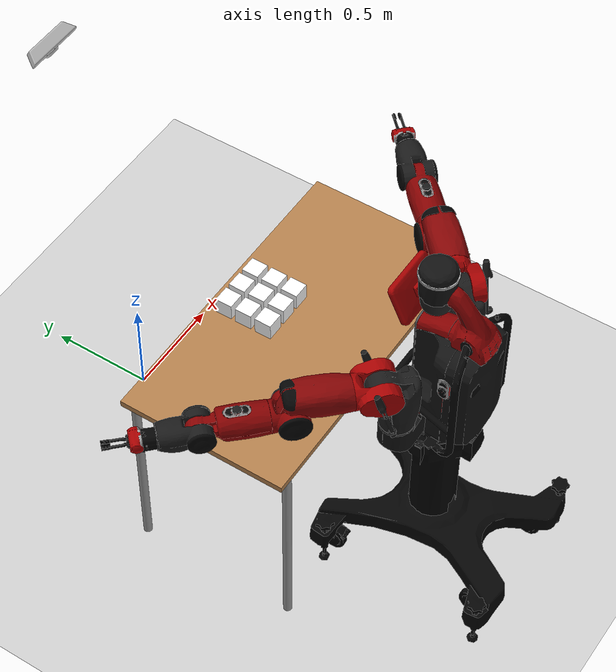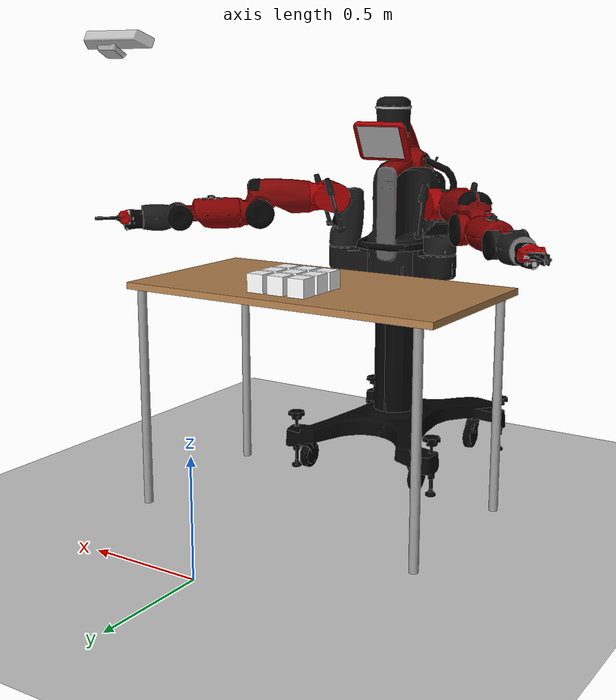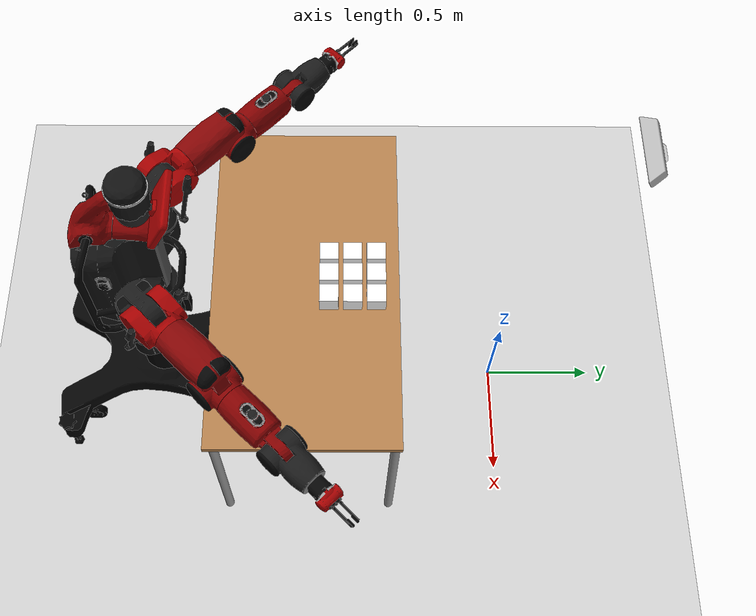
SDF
<sdf version="1.6">
 <world name="default">
  <light name="sun" type="directional">
   <pose>0 0 10 0 -0 0</pose>
   <diffuse>0.8 0.8 0.8 1</diffuse>
   <specular>0.2 0.2 0.2 1</specular>
   <attenuation>
    <range>1000</range>
    <constant>0.9</constant>
    <linear>0.01</linear>
    <quadratic>0.001</quadratic>
   </attenuation>
   <direction>-0.5 0.1 -0.9</direction>
  </light>
  <model name="ground_plane">
   <pose>0.5 -0.5 0 0 -0 0</pose>
   <static>1</static>
   <link name="link">
    <collision name="collision">
     <geometry><plane><normal>0 0 1</normal><size>100 100</size></plane></geometry>
     <surface><friction><ode><mu>100</mu><mu2>50</mu2></ode></friction></surface>
    </collision>
    <visual name="visual">
     <cast_shadows>0</cast_shadows>
     <geometry><plane><normal>0 0 1</normal><size>100 100</size></plane></geometry>
     <material>
      <script><uri>file://media/materials/scripts/gazebo.material</uri><name>Gazebo/Grey</name></script>
     </material>
    </visual>
   </link>
  </model>
  <gravity>0 0 -9.8</gravity>
  <magnetic_field>6e-06 2.3e-05 -4.2e-05</magnetic_field>
  <atmosphere type="adiabatic"/>
  <physics name="default_physics" default="0" type="ode">
   <max_step_size>0.001</max_step_size>
   <real_time_factor>1</real_time_factor>
   <real_time_update_rate>1000</real_time_update_rate>
  </physics>
  <scene><ambient>0.4 0.4 0.4 1</ambient><background>0.7 0.7 0.7 1</background><shadows>1</shadows></scene>
  <spherical_coordinates>
   <surface_model>EARTH_WGS84</surface_model>
   <latitude_deg>0</latitude_deg>
   <longitude_deg>0</longitude_deg>
   <elevation>0</elevation>
   <heading_deg>0</heading_deg>
  </spherical_coordinates>
  <model name="kinect">
   <pose>0 0.3 2 -0 0.5 -1.57</pose>
   <link name="link">
    <inertial>
     <mass>0.1</mass>
     <inertia><ixx>1</ixx><ixy>0</ixy><ixz>0</ixz><iyy>1</iyy><iyz>0</iyz><izz>1</izz></inertia>
    </inertial>
    <collision name="collision"><geometry><box><size>0.073 0.276 0.072</size></box></geometry></collision>
    <visual name="visual"><geometry><mesh><uri>model://kinect/meshes/kinect.dae</uri></mesh></geometry></visual>
    <sensor name="camera" type="depth">
     <update_rate>20</update_rate>
     <camera name="__default__">
      <horizontal_fov>1.0472</horizontal_fov>
      <image><width>640</width><height>480</height><format>R8G8B8</format></image>
      <clip><near>0.05</near><far>3</far></clip>
     </camera>
     <plugin name="camera_plugin" filename="libgazebo_ros_openni_kinect.so">
      <baseline>0.2</baseline>
      <alwaysOn>1</alwaysOn>
      <updateRate>0.0</updateRate>
      <cameraName>camera_ir</cameraName>
      <imageTopicName>/camera/depth/image_raw</imageTopicName>
      <cameraInfoTopicName>/camera/depth/camera_info</cameraInfoTopicName>
      <depthImageTopicName>/camera/depth/image_raw</depthImageTopicName>
      <depthImageInfoTopicName>/camera/depth/camera_info</depthImageInfoTopicName>
      <pointCloudTopicName>/camera/depth/points</pointCloudTopicName>
      <frameName>camera_link</frameName>
      <pointCloudCutoff>0.05</pointCloudCutoff>
      <distortionK1>0</distortionK1>
      <distortionK2>0</distortionK2>
      <distortionK3>0</distortionK3>
      <distortionT1>0</distortionT1>
      <distortionT2>0</distortionT2>
      <CxPrime>0</CxPrime>
      <Cx>0</Cx>
      <Cy>0</Cy>
      <focalLength>0</focalLength>
      <hackBaseline>0</hackBaseline>
     </plugin>
    </sensor>
    <gravity>0</gravity>
   </link>
   <static>1</static>
  </model>
  <light name="user_directional_light_0" type="directional">
   <pose>0 1 1.5 -1.57 0 0</pose>
   <diffuse>0.5 0.5 0.5 1</diffuse>
   <specular>0.1 0.1 0.1 1</specular>
   <direction>0.1 0.1 -0.9</direction>
   <attenuation>
    <range>20</range>
    <constant>0.5</constant>
    <linear>0.01</linear>
    <quadratic>0.001</quadratic>
   </attenuation>
  </light>
  <audio><device>default</device></audio>
  <model name="baxter">
   <link name="base">
    <inertial>
     <pose>0 -0 3e-06 0 -0 0</pose>
     <mass>96.2011</mass>
     <inertia>
      <ixx>6.91297</ixx>
      <ixy>0.00068017</ixy>
      <ixz>0.64779</ixz>
      <iyy>7.74978</iyy>
      <iyz>0.00434511</iyz>
      <izz>5.76418</izz>
     </inertia>
    </inertial>
    <collision name="base_fixed_joint_lump__collision_head_link_1_collision">
     <pose>0.04 -0.04 0.75 0 -0 0</pose>
     <geometry><sphere><radius>0.22</radius></sphere></geometry>
    </collision>
    <collision name="base_fixed_joint_lump__collision_head_link_2_collision_1">
     <pose>0.04 0.04 0.75 0 -0 0</pose>
     <geometry><sphere><radius>0.22</radius></sphere></geometry>
    </collision>
    <collision name="base_fixed_joint_lump__torso_collision_2">
     <geometry>
      <mesh>
       <scale>1 1 1</scale>
       <uri>/home/robot/workspace/tsn_sfc/catkin_wb/src/rethink_robotics/baxter_common/baxter_description/meshes/torso/base_link_collision.DAE</uri>
      </mesh>
     </geometry>
    </collision>
    <collision name="base_fixed_joint_lump__pedestal_collision_3">
     <geometry>
      <mesh>
       <scale>1 1 1</scale>
       <uri>/home/robot/workspace/tsn_sfc/catkin_wb/src/rethink_robotics/baxter_common/baxter_description/meshes/base/pedestal_link_collision.DAE</uri>
      </mesh>
     </geometry>
    </collision>
    <collision name="base_fixed_joint_lump__sonar_ring_collision_4">
     <pose>0.0947 0 0.817 0 -0 0</pose>
     <geometry><sphere><radius>0.001</radius></sphere></geometry>
    </collision>
    <visual name="base_fixed_joint_lump__collision_head_link_1_visual">
     <pose>0.11 0 0.75 0 -0 0</pose>
     <geometry><sphere><radius>0.001</radius></sphere></geometry>
    </visual>
    <visual name="base_fixed_joint_lump__collision_head_link_2_visual_1">
     <pose>0.11 0 0.75 0 -0 0</pose>
     <geometry><sphere><radius>0.001</radius></sphere></geometry>
    </visual>
    <visual name="base_fixed_joint_lump__torso_visual_2">
     <geometry>
      <mesh>
       <scale>1 1 1</scale>
       <uri>/home/robot/workspace/tsn_sfc/catkin_wb/src/rethink_robotics/baxter_common/baxter_description/meshes/torso/base_link.DAE</uri>
      </mesh>
     </geometry>
     <material><script><uri>__default__</uri><name>__default__</name></script></material>
    </visual>
    <visual name="base_fixed_joint_lump__pedestal_visual_3">
     <geometry>
      <mesh>
       <scale>1 1 1</scale>
       <uri>/home/robot/workspace/tsn_sfc/catkin_wb/src/rethink_robotics/baxter_common/baxter_description/meshes/base/PEDESTAL.DAE</uri>
      </mesh>
     </geometry>
    </visual>
    <visual name="base_fixed_joint_lump__sonar_ring_visual_4">
     <pose>0.06 0 0.82653 0 -0 0</pose>
     <geometry><cylinder><length>0.01</length><radius>0.085</radius></cylinder></geometry>
     <material><script><uri>__default__</uri><name>__default__</name></script></material>
    </visual>
    <self_collide>1</self_collide>
    <sensor name="sonar" type="ray">
     <ray>
      <scan>
       <horizontal>
        <samples>12</samples>
        <resolution>1</resolution>
        <min_angle>-3.14</min_angle>
        <max_angle>3.14</max_angle>
       </horizontal>
       <vertical>
        <samples>2</samples>
        <resolution>1</resolution>
        <min_angle>-0.001</min_angle>
        <max_angle>0</max_angle>
       </vertical>
      </scan>
      <range><min>0.05</min><max>50</max></range>
     </ray>
     <plugin name="sonar_plugin" filename="libgazebo_ros_block_laser.so">
      <gaussianNoise>0.00</gaussianNoise>
      <alwaysOn>1</alwaysOn>
      <updateRate>100.0</updateRate>
      <topicName>/robot/sonar/head_sonar/state</topicName>
      <frameName>sonar_ring</frameName>
      <hokuyoMinIntensity>101</hokuyoMinIntensity>
      <robotNamespace>/</robotNamespace>
     </plugin>
     <always_on>1</always_on>
     <update_rate>100</update_rate>
     <pose>0.0947 0 0.817 0 -0 0</pose>
    </sensor>
   </link>
   <joint name="fixed" type="fixed"><child>base</child><parent>world</parent></joint>
   <link name="head">
    <pose>0.06 0 0.686 0 -0 0</pose>
    <inertial>
     <pose>0.054677 0 5e-06 0 -0 0</pose>
     <mass>0.988238</mass>
     <inertia>
      <ixx>0.00620194</ixx>
      <ixy>0.000202093</ixy>
      <ixz>0.000495898</ixz>
      <iyy>0.010977</iyy>
      <iyz>-0.00109806</iyz>
      <izz>0.00983914</izz>
     </inertia>
    </inertial>
    <collision name="head_collision"><geometry><sphere><radius>0.001</radius></sphere></geometry></collision>
    <collision name="head_fixed_joint_lump__screen_collision_1">
     <pose>0.1227 0 0 1.75057 0 1.5708</pose>
     <geometry><sphere><radius>0.001</radius></sphere></geometry>
    </collision>
    <visual name="head_visual">
     <pose>0 0 0.00953 0 -0 0</pose>
     <geometry>
      <mesh>
       <scale>1 1 1</scale>
       <uri>/home/robot/workspace/tsn_sfc/catkin_wb/src/rethink_robotics/baxter_common/baxter_description/meshes/head/H0.DAE</uri>
      </mesh>
     </geometry>
    </visual>
    <visual name="head_fixed_joint_lump__screen_visual_1">
     <pose>0.086855 0 -0.003172 1.5708 0.179774 0</pose>
     <geometry>
      <mesh>
       <scale>1 1 1</scale>
       <uri>/home/robot/workspace/tsn_sfc/catkin_wb/src/rethink_robotics/baxter_common/baxter_description/meshes/head/H1.DAE</uri>
      </mesh>
     </geometry>
    </visual>
    <visual name="head_fixed_joint_lump__display_visual_2">
     <pose>0.119839 0 -0.015742 2.01237 0 1.5708</pose>
     <geometry><box><size>0.218 0.16 0.001</size></box></geometry>
     <plugin name="screen_video_controller" filename="libgazebo_ros_video.so">
      <height>600</height>
      <width>1024</width>
      <topicName>/robot/xdisplay</topicName>
      <robotNamespace>/robot</robotNamespace>
     </plugin>
     <material><script><uri>__default__</uri><name>__default__</name></script></material>
    </visual>
    <sensor name="head_camera" type="camera">
     <update_rate>30</update_rate>
     <camera name="head_camera">
      <pose>0 0.21 0 -0 -0.8 -1.5708</pose>
      <horizontal_fov>1.39626</horizontal_fov>
      <image><width>800</width><height>800</height><format>R8G8B8</format></image>
      <clip><near>0.02</near><far>300</far></clip>
      <noise><type>gaussian</type><mean>0</mean><stddev>0.007</stddev></noise>
     </camera>
     <plugin name="camera_controller" filename="libgazebo_ros_camera.so">
      <alwaysOn>1</alwaysOn>
      <updateRate>0.0</updateRate>
      <cameraName>head_camera</cameraName>
      <imageTopicName>image</imageTopicName>
      <cameraInfoTopicName>camera_info</cameraInfoTopicName>
      <frameName>head_camera</frameName>
      <hackBaseline>0.07</hackBaseline>
      <distortionK1>0.0</distortionK1>
      <distortionK2>0.0</distortionK2>
      <distortionK3>0.0</distortionK3>
      <distortionT1>0.0</distortionT1>
      <distortionT2>0.0</distortionT2>
      <CxPrime>0</CxPrime>
      <Cx>0.0</Cx>
      <Cy>0.0</Cy>
      <focalLength>0.0</focalLength>
      <robotNamespace>/cameras</robotNamespace>
     </plugin>
     <pose>0.12839 0 0.06368 1.75057 0 1.5708</pose>
    </sensor>
   </link>
   <joint name="head_pan" type="revolute">
    <child>head</child>
    <parent>base</parent>
    <axis>
     <xyz>0 0 1</xyz>
     <limit><lower>-1.3963</lower><upper>1.3963</upper><effort>50000</effort><velocity>10000</velocity></limit>
     <dynamics>
      <damping>0.7</damping>
      <friction>0</friction>
      <spring_reference>0</spring_reference>
      <spring_stiffness>0</spring_stiffness>
     </dynamics>
     <use_parent_model_frame>1</use_parent_model_frame>
    </axis>
    <physics>
     <ode>
      <implicit_spring_damper>1</implicit_spring_damper>
      <cfm_damping>1</cfm_damping>
      <limit><cfm>0</cfm><erp>0.2</erp></limit>
     </ode>
    </physics>
   </joint>
   <link name="left_upper_shoulder">
    <pose>0.064027 0.259027 0.129626 0 -0 0.7854</pose>
    <inertial>
     <pose>0.01783 0.00086 0.19127 0 -0 0</pose>
     <mass>5.70044</mass>
     <inertia>
      <ixx>0.047091</ixx>
      <ixy>0.000127876</ixy>
      <ixz>0.0061487</ixz>
      <iyy>0.0376698</iyy>
      <iyz>0.000780869</iyz>
      <izz>0.0359599</izz>
     </inertia>
    </inertial>
    <collision name="left_upper_shoulder_collision">
     <pose>0 0 0.1361 0 -0 0</pose>
     <geometry><cylinder><length>0.2722</length><radius>0.06</radius></cylinder></geometry>
    </collision>
    <visual name="left_upper_shoulder_visual">
     <geometry>
      <mesh>
       <scale>1 1 1</scale>
       <uri>/home/robot/workspace/tsn_sfc/catkin_wb/src/rethink_robotics/baxter_common/baxter_description/meshes/upper_shoulder/S0.DAE</uri>
      </mesh>
     </geometry>
    </visual>
   </link>
   <joint name="left_s0" type="revolute">
    <child>left_upper_shoulder</child>
    <parent>base</parent>
    <axis>
     <xyz>0 0 1</xyz>
     <limit><lower>-1.70168</lower><upper>1.70168</upper><effort>50</effort><velocity>1.5</velocity></limit>
     <dynamics>
      <damping>0.7</damping>
      <friction>0</friction>
      <spring_reference>0</spring_reference>
      <spring_stiffness>0</spring_stiffness>
     </dynamics>
     <use_parent_model_frame>1</use_parent_model_frame>
    </axis>
    <physics>
     <ode>
      <implicit_spring_damper>1</implicit_spring_damper>
      <cfm_damping>1</cfm_damping>
      <limit><cfm>0</cfm><erp>0.2</erp></limit>
     </ode>
    </physics>
   </joint>
   <link name="left_lower_shoulder">
    <pose>0.112818 0.307818 0.399976 -1.5708 -0 0.7854</pose>
    <inertial>
     <pose>0.068451 0.00269 -0.00529 0 -0 0</pose>
     <mass>3.22708</mass>
     <inertia>
      <ixx>0.0117521</ixx>
      <ixy>-0.000300954</ixy>
      <ixz>0.00207674</ixz>
      <iyy>0.0278861</iyy>
      <iyz>-0.000188219</iyz>
      <izz>0.0207877</izz>
     </inertia>
    </inertial>
    <collision name="left_lower_shoulder_collision">
     <geometry><cylinder><length>0.12</length><radius>0.06</radius></cylinder></geometry>
    </collision>
    <collision name="left_lower_shoulder_fixed_joint_lump__left_upper_elbow_visual_collision_1">
     <pose>0.2435 -0 0 1.5708 -0 1.5708</pose>
     <geometry><cylinder><length>0.273</length><radius>0.06</radius></cylinder></geometry>
    </collision>
    <visual name="left_lower_shoulder_visual">
     <geometry>
      <mesh>
       <scale>1 1 1</scale>
       <uri>/home/robot/workspace/tsn_sfc/catkin_wb/src/rethink_robotics/baxter_common/baxter_description/meshes/lower_shoulder/S1.DAE</uri>
      </mesh>
     </geometry>
    </visual>
   </link>
   <joint name="left_s1" type="revolute">
    <child>left_lower_shoulder</child>
    <parent>left_upper_shoulder</parent>
    <axis>
     <xyz>-0.707108 0.707105 0</xyz>
     <limit><lower>-2.147</lower><upper>1.047</upper><effort>50</effort><velocity>1.5</velocity></limit>
     <dynamics>
      <damping>0.7</damping>
      <friction>0</friction>
      <spring_reference>0</spring_reference>
      <spring_stiffness>0</spring_stiffness>
     </dynamics>
     <use_parent_model_frame>1</use_parent_model_frame>
    </axis>
    <physics>
     <ode>
      <implicit_spring_damper>1</implicit_spring_damper>
      <cfm_damping>1</cfm_damping>
      <limit><cfm>0</cfm><erp>0.2</erp></limit>
     </ode>
    </physics>
   </joint>
   <link name="left_upper_elbow">
    <pose>0.184942 0.379943 0.399976 2.35619 1.57079 3.14159</pose>
    <inertial>
     <pose>-0.00276 0.00132 0.18086 0 -0 0</pose>
     <mass>4.31272</mass>
     <inertia>
      <ixx>0.0266173</ixx>
      <ixy>0.000292706</ixy>
      <ixz>0.0039219</ixz>
      <iyy>0.0284436</iyy>
      <iyz>0.00108389</iyz>
      <izz>0.0124801</izz>
     </inertia>
    </inertial>
    <collision name="left_upper_elbow_collision">
     <pose>0 0 -0.0535 0 -0 0</pose>
     <geometry><cylinder><length>0.107</length><radius>0.06</radius></cylinder></geometry>
    </collision>
    <visual name="left_upper_elbow_visual">
     <geometry>
      <mesh>
       <scale>1 1 1</scale>
       <uri>/home/robot/workspace/tsn_sfc/catkin_wb/src/rethink_robotics/baxter_common/baxter_description/meshes/upper_elbow/E0.DAE</uri>
      </mesh>
     </geometry>
    </visual>
   </link>
   <joint name="left_e0" type="revolute">
    <child>left_upper_elbow</child>
    <parent>left_lower_shoulder</parent>
    <axis>
     <xyz>0.707105 0.707108 0</xyz>
     <limit><lower>-3.05418</lower><upper>3.05418</upper><effort>50</effort><velocity>1.5</velocity></limit>
     <dynamics>
      <damping>0.7</damping>
      <friction>0</friction>
      <spring_reference>0</spring_reference>
      <spring_stiffness>0</spring_stiffness>
     </dynamics>
     <use_parent_model_frame>1</use_parent_model_frame>
    </axis>
    <physics>
     <ode>
      <implicit_spring_damper>1</implicit_spring_damper>
      <cfm_damping>1</cfm_damping>
      <limit><cfm>0</cfm><erp>0.2</erp></limit>
     </ode>
    </physics>
   </joint>
   <link name="left_lower_elbow">
    <pose>0.370501 0.565502 0.330976 -1.5708 -0 0.7854</pose>
    <inertial>
     <pose>0.026113 0.00159 -0.01117 0 -0 0</pose>
     <mass>2.07216</mass>
     <inertia>
      <ixx>0.00711585</ixx>
      <ixy>0.000360372</ixy>
      <ixz>0.00074588</ixz>
      <iyy>0.0131827</iyy>
      <iyz>-0.000196632</iyz>
      <izz>0.00926891</izz>
     </inertia>
    </inertial>
    <collision name="left_lower_elbow_collision">
     <geometry><cylinder><length>0.1</length><radius>0.06</radius></cylinder></geometry>
    </collision>
    <collision name="left_lower_elbow_fixed_joint_lump__left_upper_forearm_visual_collision_1">
     <pose>0.224 -0 0 1.5708 -0 1.5708</pose>
     <geometry><cylinder><length>0.272</length><radius>0.06</radius></cylinder></geometry>
    </collision>
    <visual name="left_lower_elbow_visual">
     <geometry>
      <mesh>
       <scale>1 1 1</scale>
       <uri>/home/robot/workspace/tsn_sfc/catkin_wb/src/rethink_robotics/baxter_common/baxter_description/meshes/lower_elbow/E1.DAE</uri>
      </mesh>
     </geometry>
    </visual>
   </link>
   <joint name="left_e1" type="revolute">
    <child>left_lower_elbow</child>
    <parent>left_upper_elbow</parent>
    <axis>
     <xyz>-0.707108 0.707105 0</xyz>
     <limit><lower>-0.05</lower><upper>2.618</upper><effort>50</effort><velocity>1.5</velocity></limit>
     <dynamics>
      <damping>0.7</damping>
      <friction>0</friction>
      <spring_reference>0</spring_reference>
      <spring_stiffness>0</spring_stiffness>
     </dynamics>
     <use_parent_model_frame>1</use_parent_model_frame>
    </axis>
    <physics>
     <ode>
      <implicit_spring_damper>1</implicit_spring_damper>
      <cfm_damping>1</cfm_damping>
      <limit><cfm>0</cfm><erp>0.2</erp></limit>
     </ode>
    </physics>
   </joint>
   <link name="left_upper_forearm">
    <pose>0.44375 0.638751 0.330976 2.35619 1.57079 3.14159</pose>
    <inertial>
     <pose>-0.001682 0.0046 0.139519 0 -0 0</pose>
     <mass>2.24675</mass>
     <inertia>
      <ixx>0.0166775</ixx>
      <ixy>0.000184012</ixy>
      <ixz>0.000186469</ixz>
      <iyy>0.0167549</iyy>
      <iyz>-0.000647332</iyz>
      <izz>0.00374662</izz>
     </inertia>
    </inertial>
    <collision name="left_upper_forearm_collision">
     <pose>0 0 -0.044 0 -0 0</pose>
     <geometry><cylinder><length>0.088</length><radius>0.06</radius></cylinder></geometry>
    </collision>
    <visual name="left_upper_forearm_visual">
     <geometry>
      <mesh>
       <scale>1 1 1</scale>
       <uri>/home/robot/workspace/tsn_sfc/catkin_wb/src/rethink_robotics/baxter_common/baxter_description/meshes/upper_forearm/W0.DAE</uri>
      </mesh>
     </geometry>
    </visual>
   </link>
   <joint name="left_w0" type="revolute">
    <child>left_upper_forearm</child>
    <parent>left_lower_elbow</parent>
    <axis>
     <xyz>0.707105 0.707108 0</xyz>
     <limit><lower>-3.059</lower><upper>3.059</upper><effort>15</effort><velocity>4</velocity></limit>
     <dynamics>
      <damping>0.7</damping>
      <friction>0</friction>
      <spring_reference>0</spring_reference>
      <spring_stiffness>0</spring_stiffness>
     </dynamics>
     <use_parent_model_frame>1</use_parent_model_frame>
    </axis>
    <physics>
     <ode>
      <implicit_spring_damper>1</implicit_spring_damper>
      <cfm_damping>1</cfm_damping>
      <limit><cfm>0</cfm><erp>0.2</erp></limit>
     </ode>
    </physics>
   </joint>
   <link name="left_lower_forearm">
    <pose>0.635163 0.830166 0.320976 -1.5708 -0 0.7854</pose>
    <inertial>
     <pose>0.06041 0.00697 0.006 0 -0 0</pose>
     <mass>1.60979</mass>
     <inertia>
      <ixx>0.00387607</ixx>
      <ixy>-0.000443848</ixy>
      <ixz>-0.00021115</ixz>
      <iyy>0.00700538</iyy>
      <iyz>0.000153481</iyz>
      <izz>0.00552755</izz>
     </inertia>
    </inertial>
    <collision name="left_lower_forearm_collision">
     <geometry><cylinder><length>0.1</length><radius>0.06</radius></cylinder></geometry>
    </collision>
    <visual name="left_lower_forearm_visual">
     <geometry>
      <mesh>
       <scale>1 1 1</scale>
       <uri>/home/robot/workspace/tsn_sfc/catkin_wb/src/rethink_robotics/baxter_common/baxter_description/meshes/lower_forearm/W1.DAE</uri>
      </mesh>
     </geometry>
    </visual>
   </link>
   <joint name="left_w1" type="revolute">
    <child>left_lower_forearm</child>
    <parent>left_upper_forearm</parent>
    <axis>
     <xyz>-0.707108 0.707105 0</xyz>
     <limit><lower>-1.5708</lower><upper>2.094</upper><effort>15</effort><velocity>4</velocity></limit>
     <dynamics>
      <damping>0.7</damping>
      <friction>0</friction>
      <spring_reference>0</spring_reference>
      <spring_stiffness>0</spring_stiffness>
     </dynamics>
     <use_parent_model_frame>1</use_parent_model_frame>
    </axis>
    <physics>
     <ode>
      <implicit_spring_damper>1</implicit_spring_damper>
      <cfm_damping>1</cfm_damping>
      <limit><cfm>0</cfm><erp>0.2</erp></limit>
     </ode>
    </physics>
   </joint>
   <link name="left_wrist">
    <pose>0.71717 0.912173 0.320976 2.35619 1.57079 3.14159</pose>
    <inertial>
     <pose>0.003318 0.000616 0.079435 0 -0 0</pose>
     <mass>0.84268</mass>
     <inertia>
      <ixx>0.00285059</ixx>
      <ixy>7.17373e-06</ixy>
      <ixz>2.52032e-05</ixz>
      <iyy>0.00291735</iyy>
      <iyz>2.17353e-05</iyz>
      <izz>0.000560608</izz>
     </inertia>
    </inertial>
    <collision name="left_wrist_collision">
     <geometry><cylinder><length>0.165</length><radius>0.06</radius></cylinder></geometry>
    </collision>
    <collision name="left_wrist_fixed_joint_lump__left_hand_collision_1">
     <pose>0 0 0.09035 0 -0 0</pose>
     <geometry><cylinder><length>0.0464</length><radius>0.04</radius></cylinder></geometry>
    </collision>
    <collision name="left_wrist_fixed_joint_lump__left_gripper_base_collision_2">
     <pose>0 0 0.13855 1.5708 -0 3.14159</pose>
     <geometry><cylinder><length>0.1</length><radius>0.029</radius></cylinder></geometry>
    </collision>
    <visual name="left_wrist_visual">
     <geometry>
      <mesh>
       <scale>1 1 1</scale>
       <uri>/home/robot/workspace/tsn_sfc/catkin_wb/src/rethink_robotics/baxter_common/baxter_description/meshes/wrist/W2.DAE</uri>
      </mesh>
     </geometry>
    </visual>
    <visual name="left_wrist_fixed_joint_lump__left_gripper_base_visual_1">
     <pose>0 0 0.13855 1.5708 -0 3.14159</pose>
     <geometry>
      <mesh>
       <scale>1 1 1</scale>
       <uri>/home/robot/workspace/tsn_sfc/catkin_wb/src/rethink_robotics/baxter_common/rethink_ee_description/meshes/electric_gripper/electric_gripper_base.DAE</uri>
      </mesh>
     </geometry>
    </visual>
    <visual name="left_wrist_fixed_joint_lump__left_hand_accelerometer_visual_2">
     <pose>0.00198 0.000133 0.09895 0 -0 0</pose>
     <geometry><box><size>0.01 0.01 0.01</size></box></geometry>
    </visual>
    <visual name="left_wrist_fixed_joint_lump__left_hand_camera_visual_3">
     <pose>0.03825 0.012 0.128905 0 0 -1.5708</pose>
     <geometry><cylinder><length>0.01</length><radius>0.02</radius></cylinder></geometry>
     <material><script><uri>__default__</uri><name>__default__</name></script></material>
    </visual>
    <visual name="left_wrist_fixed_joint_lump__left_hand_range_visual_4">
     <pose>0.032 -0.020245 0.14235 3.14159 -1.57079 1.57079</pose>
     <geometry><box><size>0.005 0.02 0.005</size></box></geometry>
     <material><script><uri>__default__</uri><name>__default__</name></script></material>
    </visual>
    <sensor name="left_hand_camera" type="camera">
     <update_rate>30</update_rate>
     <camera name="left_hand_camera">
      <pose>0 0 0 -1.57079 -1.57079 3.14159</pose>
      <horizontal_fov>1.39626</horizontal_fov>
      <image><width>800</width><height>800</height><format>R8G8B8</format></image>
      <clip><near>0.02</near><far>300</far></clip>
      <noise><type>gaussian</type><mean>0</mean><stddev>0.007</stddev></noise>
     </camera>
     <plugin name="camera_controller" filename="libgazebo_ros_camera.so">
      <alwaysOn>1</alwaysOn>
      <updateRate>0.0</updateRate>
      <cameraName>left_hand_camera</cameraName>
      <imageTopicName>image</imageTopicName>
      <cameraInfoTopicName>camera_info</cameraInfoTopicName>
      <frameName>left_hand_camera</frameName>
      <hackBaseline>0.07</hackBaseline>
      <distortionK1>0.0</distortionK1>
      <distortionK2>0.0</distortionK2>
      <distortionK3>0.0</distortionK3>
      <distortionT1>0.0</distortionT1>
      <distortionT2>0.0</distortionT2>
      <CxPrime>0</CxPrime>
      <Cx>0.0</Cx>
      <Cy>0.0</Cy>
      <focalLength>0.0</focalLength>
      <robotNamespace>/cameras</robotNamespace>
     </plugin>
     <pose>0.03825 0.012 0.128905 0 0 -1.5708</pose>
    </sensor>
    <gravity>0</gravity>
    <sensor name="ir_left" type="ray">
     <ray>
      <scan>
       <horizontal>
        <samples>1</samples>
        <resolution>1</resolution>
        <min_angle>-0.5</min_angle>
        <max_angle>0.5</max_angle>
       </horizontal>
       <vertical><samples>1</samples><min_angle>0</min_angle><max_angle>0</max_angle></vertical>
      </scan>
      <range><min>0.004</min><max>0.4</max></range>
     </ray>
     <plugin name="plugin_4" filename="libgazebo_ros_laser.so">
      <gaussianNoise>0.005</gaussianNoise>
      <alwaysOn>1</alwaysOn>
      <updateRate>100</updateRate>
      <topicName>/sim/laserscan/left_hand_range/state</topicName>
      <frameName>left_hand_range</frameName>
      <robotNamespace>/</robotNamespace>
     </plugin>
     <always_on>1</always_on>
     <update_rate>100</update_rate>
     <pose>0.032 -0.020245 0.14235 3.14159 -1.57079 1.57079</pose>
    </sensor>
   </link>
   <joint name="left_w2" type="revolute">
    <child>left_wrist</child>
    <parent>left_lower_forearm</parent>
    <axis>
     <xyz>0.707105 0.707108 0</xyz>
     <limit><lower>-3.059</lower><upper>3.059</upper><effort>15</effort><velocity>4</velocity></limit>
     <dynamics>
      <damping>0.7</damping>
      <friction>0</friction>
      <spring_reference>0</spring_reference>
      <spring_stiffness>0</spring_stiffness>
     </dynamics>
     <use_parent_model_frame>1</use_parent_model_frame>
    </axis>
    <physics>
     <ode>
      <implicit_spring_damper>1</implicit_spring_damper>
      <cfm_damping>1</cfm_damping>
      <limit><cfm>0</cfm><erp>0.2</erp></limit>
     </ode>
    </physics>
   </joint>
   <link name="l_gripper_l_finger">
    <pose>0.830342 1.02322 0.320976 2.35619 1.57079 3.14159</pose>
    <inertial>
     <pose>0 0.00575 0.037567 0 -0 3.14159</pose>
     <mass>0.03</mass>
     <inertia>
      <ixx>0.0200867</ixx>
      <ixy>4.0989e-19</ixy>
      <ixz>-2.67795e-18</ixz>
      <iyy>0.0200847</iyy>
      <iyz>1.29605e-05</iyz>
      <izz>0.020002</izz>
     </inertia>
    </inertial>
    <collision name="l_gripper_l_finger_collision">
     <pose>0 0.01725 0.0615 0 -0 3.14159</pose>
     <geometry><box><size>0.01 0.0135 0.1127</size></box></geometry>
     <surface>
      <contact><ode><kp>100000</kp><kd>1</kd></ode></contact>
      <friction><ode><mu>1000</mu><mu2>1000</mu2><fdir1>0 0 1</fdir1></ode></friction>
     </surface>
    </collision>
    <collision name="l_gripper_l_finger_collision_1">
     <pose>-0.005 -0.003 0.0083 0 -0 3.14159</pose>
     <geometry><box><size>0.01 0.05 0.017</size></box></geometry>
     <surface>
      <contact><ode><kp>100000</kp><kd>1</kd></ode></contact>
      <friction><ode><mu>1000</mu><mu2>1000</mu2><fdir1>0 0 1</fdir1></ode></friction>
     </surface>
    </collision>
    <collision name="l_gripper_l_finger_tip_collision_2">
     <pose>0 0.01275 0.0977 0 -0 -3.14159</pose>
     <geometry><box><size>0.042 0.0065 0.037</size></box></geometry>
     <surface>
      <contact><ode><kp>100000</kp><kd>1</kd></ode></contact>
      <friction><ode><mu>1000</mu><mu2>1000</mu2><fdir1>0 0 1</fdir1></ode></friction>
     </surface>
    </collision>
    <visual name="l_gripper_l_finger_visual">
     <pose>0 0 0 0 -0 3.14159</pose>
     <geometry>
      <mesh>
       <scale>1 1 1</scale>
       <uri>/home/robot/workspace/tsn_sfc/catkin_wb/src/rethink_robotics/baxter_common/rethink_ee_description/meshes/electric_gripper/fingers/extended_narrow.DAE</uri>
      </mesh>
     </geometry>
     <material><script><uri>__default__</uri><name>__default__</name></script></material>
    </visual>
    <visual name="l_gripper_l_finger_tip_visual_1">
     <pose>0 0.01725 0.1127 0 -0 -3.14159</pose>
     <geometry>
      <mesh>
       <scale>1 1 1</scale>
       <uri>/home/robot/workspace/tsn_sfc/catkin_wb/src/rethink_robotics/baxter_common/rethink_ee_description/meshes/electric_gripper/fingers/paddle_tip.DAE</uri>
      </mesh>
     </geometry>
     <material><script><uri>__default__</uri><name>__default__</name></script></material>
    </visual>
   </link>
   <joint name="l_gripper_l_finger_joint" type="prismatic">
    <child>l_gripper_l_finger</child>
    <parent>left_wrist</parent>
    <axis>
     <xyz>-0.707108 0.707105 0</xyz>
     <limit><lower>0</lower><upper>0.020833</upper><effort>20</effort><velocity>5</velocity></limit>
     <dynamics>
      <damping>0.7</damping>
      <friction>0</friction>
      <spring_reference>0</spring_reference>
      <spring_stiffness>0</spring_stiffness>
     </dynamics>
     <use_parent_model_frame>1</use_parent_model_frame>
    </axis>
    <physics>
     <ode>
      <implicit_spring_damper>1</implicit_spring_damper>
      <cfm_damping>1</cfm_damping>
      <limit><cfm>0</cfm><erp>0.2</erp></limit>
     </ode>
    </physics>
   </joint>
   <link name="l_gripper_r_finger">
    <pose>0.828221 1.02535 0.320976 2.35619 1.57079 3.14159</pose>
    <inertial>
     <pose>0 -0.00575 0.037567 0 -0 0</pose>
     <mass>0.03</mass>
     <inertia>
      <ixx>0.0200867</ixx>
      <ixy>0</ixy>
      <ixz>0</ixz>
      <iyy>0.0200847</iyy>
      <iyz>1.29605e-05</iyz>
      <izz>0.020002</izz>
     </inertia>
    </inertial>
    <collision name="l_gripper_r_finger_collision">
     <pose>0 -0.01725 0.0615 0 -0 0</pose>
     <geometry><box><size>0.01 0.0135 0.1127</size></box></geometry>
     <surface>
      <contact><ode><kp>100000</kp><kd>1</kd></ode></contact>
      <friction><ode><mu>1000</mu><mu2>1000</mu2><fdir1>0 0 1</fdir1></ode></friction>
     </surface>
    </collision>
    <collision name="l_gripper_r_finger_collision_1">
     <pose>0.005 0.003 0.0083 0 -0 0</pose>
     <geometry><box><size>0.01 0.05 0.017</size></box></geometry>
     <surface>
      <contact><ode><kp>100000</kp><kd>1</kd></ode></contact>
      <friction><ode><mu>1000</mu><mu2>1000</mu2><fdir1>0 0 1</fdir1></ode></friction>
     </surface>
    </collision>
    <collision name="l_gripper_r_finger_tip_collision_2">
     <pose>0 -0.01275 0.0977 0 -0 0</pose>
     <geometry><box><size>0.042 0.0065 0.037</size></box></geometry>
     <surface>
      <contact><ode><kp>100000</kp><kd>1</kd></ode></contact>
      <friction><ode><mu>1000</mu><mu2>1000</mu2><fdir1>0 0 1</fdir1></ode></friction>
     </surface>
    </collision>
    <visual name="l_gripper_r_finger_visual">
     <geometry>
      <mesh>
       <scale>1 1 1</scale>
       <uri>/home/robot/workspace/tsn_sfc/catkin_wb/src/rethink_robotics/baxter_common/rethink_ee_description/meshes/electric_gripper/fingers/extended_narrow.DAE</uri>
      </mesh>
     </geometry>
     <material><script><uri>__default__</uri><name>__default__</name></script></material>
    </visual>
    <visual name="l_gripper_r_finger_tip_visual_1">
     <pose>0 -0.01725 0.1127 0 -0 0</pose>
     <geometry>
      <mesh>
       <scale>1 1 1</scale>
       <uri>/home/robot/workspace/tsn_sfc/catkin_wb/src/rethink_robotics/baxter_common/rethink_ee_description/meshes/electric_gripper/fingers/paddle_tip.DAE</uri>
      </mesh>
     </geometry>
     <material><script><uri>__default__</uri><name>__default__</name></script></material>
    </visual>
   </link>
   <joint name="l_gripper_r_finger_joint" type="prismatic">
    <child>l_gripper_r_finger</child>
    <parent>left_wrist</parent>
    <axis>
     <xyz>-0.707108 0.707105 0</xyz>
     <limit><lower>-0.020833</lower><upper>0</upper><effort>20</effort><velocity>5</velocity></limit>
     <dynamics>
      <damping>0.7</damping>
      <friction>0</friction>
      <spring_reference>0</spring_reference>
      <spring_stiffness>0</spring_stiffness>
     </dynamics>
     <use_parent_model_frame>1</use_parent_model_frame>
    </axis>
    <physics>
     <ode>
      <implicit_spring_damper>1</implicit_spring_damper>
      <cfm_damping>1</cfm_damping>
      <limit><cfm>0</cfm><erp>0.2</erp></limit>
     </ode>
    </physics>
   </joint>
   <link name="right_upper_shoulder">
    <pose>0.064027 -0.259027 0.129626 0 0 -0.7854</pose>
    <inertial>
     <pose>0.01783 0.00086 0.19127 0 -0 0</pose>
     <mass>5.70044</mass>
     <inertia>
      <ixx>0.047091</ixx>
      <ixy>0.000127876</ixy>
      <ixz>0.0061487</ixz>
      <iyy>0.0376698</iyy>
      <iyz>0.000780869</iyz>
      <izz>0.0359599</izz>
     </inertia>
    </inertial>
    <collision name="right_upper_shoulder_collision">
     <pose>0 0 0.1361 0 -0 0</pose>
     <geometry><cylinder><length>0.2722</length><radius>0.06</radius></cylinder></geometry>
    </collision>
    <visual name="right_upper_shoulder_visual">
     <geometry>
      <mesh>
       <scale>1 1 1</scale>
       <uri>/home/robot/workspace/tsn_sfc/catkin_wb/src/rethink_robotics/baxter_common/baxter_description/meshes/upper_shoulder/S0.DAE</uri>
      </mesh>
     </geometry>
    </visual>
   </link>
   <joint name="right_s0" type="revolute">
    <child>right_upper_shoulder</child>
    <parent>base</parent>
    <axis>
     <xyz>0 0 1</xyz>
     <limit><lower>-1.70168</lower><upper>1.70168</upper><effort>50</effort><velocity>1.5</velocity></limit>
     <dynamics>
      <damping>0.7</damping>
      <friction>0</friction>
      <spring_reference>0</spring_reference>
      <spring_stiffness>0</spring_stiffness>
     </dynamics>
     <use_parent_model_frame>1</use_parent_model_frame>
    </axis>
    <physics>
     <ode>
      <implicit_spring_damper>1</implicit_spring_damper>
      <cfm_damping>1</cfm_damping>
      <limit><cfm>0</cfm><erp>0.2</erp></limit>
     </ode>
    </physics>
   </joint>
   <link name="right_lower_shoulder">
    <pose>0.112818 -0.307818 0.399976 -1.5708 -0 -0.7854</pose>
    <inertial>
     <pose>0.068451 0.00269 -0.00529 0 -0 0</pose>
     <mass>3.22708</mass>
     <inertia>
      <ixx>0.0117521</ixx>
      <ixy>-0.000300954</ixy>
      <ixz>0.00207674</ixz>
      <iyy>0.0278861</iyy>
      <iyz>-0.000188219</iyz>
      <izz>0.0207877</izz>
     </inertia>
    </inertial>
    <collision name="right_lower_shoulder_collision">
     <geometry><cylinder><length>0.12</length><radius>0.06</radius></cylinder></geometry>
    </collision>
    <collision name="right_lower_shoulder_fixed_joint_lump__right_upper_elbow_visual_collision_1">
     <pose>0.2435 -0 0 1.5708 -0 1.5708</pose>
     <geometry><cylinder><length>0.273</length><radius>0.06</radius></cylinder></geometry>
    </collision>
    <visual name="right_lower_shoulder_visual">
     <geometry>
      <mesh>
       <scale>1 1 1</scale>
       <uri>/home/robot/workspace/tsn_sfc/catkin_wb/src/rethink_robotics/baxter_common/baxter_description/meshes/lower_shoulder/S1.DAE</uri>
      </mesh>
     </geometry>
    </visual>
   </link>
   <joint name="right_s1" type="revolute">
    <child>right_lower_shoulder</child>
    <parent>right_upper_shoulder</parent>
    <axis>
     <xyz>0.707108 0.707105 0</xyz>
     <limit><lower>-2.147</lower><upper>1.047</upper><effort>50</effort><velocity>1.5</velocity></limit>
     <dynamics>
      <damping>0.7</damping>
      <friction>0</friction>
      <spring_reference>0</spring_reference>
      <spring_stiffness>0</spring_stiffness>
     </dynamics>
     <use_parent_model_frame>1</use_parent_model_frame>
    </axis>
    <physics>
     <ode>
      <implicit_spring_damper>1</implicit_spring_damper>
      <cfm_damping>1</cfm_damping>
      <limit><cfm>0</cfm><erp>0.2</erp></limit>
     </ode>
    </physics>
   </joint>
   <link name="right_upper_elbow">
    <pose>0.184942 -0.379943 0.399976 -2.35619 1.57079 3.14159</pose>
    <inertial>
     <pose>-0.00276 0.00132 0.18086 0 -0 0</pose>
     <mass>4.31272</mass>
     <inertia>
      <ixx>0.0266173</ixx>
      <ixy>0.000292706</ixy>
      <ixz>0.0039219</ixz>
      <iyy>0.0284436</iyy>
      <iyz>0.00108389</iyz>
      <izz>0.0124801</izz>
     </inertia>
    </inertial>
    <collision name="right_upper_elbow_collision">
     <pose>0 0 -0.0535 0 -0 0</pose>
     <geometry><cylinder><length>0.107</length><radius>0.06</radius></cylinder></geometry>
    </collision>
    <visual name="right_upper_elbow_visual">
     <geometry>
      <mesh>
       <scale>1 1 1</scale>
       <uri>/home/robot/workspace/tsn_sfc/catkin_wb/src/rethink_robotics/baxter_common/baxter_description/meshes/upper_elbow/E0.DAE</uri>
      </mesh>
     </geometry>
    </visual>
   </link>
   <joint name="right_e0" type="revolute">
    <child>right_upper_elbow</child>
    <parent>right_lower_shoulder</parent>
    <axis>
     <xyz>0.707105 -0.707108 0</xyz>
     <limit><lower>-3.05418</lower><upper>3.05418</upper><effort>50</effort><velocity>1.5</velocity></limit>
     <dynamics>
      <damping>0.7</damping>
      <friction>0</friction>
      <spring_reference>0</spring_reference>
      <spring_stiffness>0</spring_stiffness>
     </dynamics>
     <use_parent_model_frame>1</use_parent_model_frame>
    </axis>
    <physics>
     <ode>
      <implicit_spring_damper>1</implicit_spring_damper>
      <cfm_damping>1</cfm_damping>
      <limit><cfm>0</cfm><erp>0.2</erp></limit>
     </ode>
    </physics>
   </joint>
   <link name="right_lower_elbow">
    <pose>0.370501 -0.565502 0.330976 -1.5708 -0 -0.7854</pose>
    <inertial>
     <pose>0.026113 0.00159 -0.01117 0 -0 0</pose>
     <mass>2.07216</mass>
     <inertia>
      <ixx>0.00711585</ixx>
      <ixy>0.000360372</ixy>
      <ixz>0.00074588</ixz>
      <iyy>0.0131827</iyy>
      <iyz>-0.000196632</iyz>
      <izz>0.00926891</izz>
     </inertia>
    </inertial>
    <collision name="right_lower_elbow_collision">
     <geometry><cylinder><length>0.1</length><radius>0.06</radius></cylinder></geometry>
    </collision>
    <collision name="right_lower_elbow_fixed_joint_lump__right_upper_forearm_visual_collision_1">
     <pose>0.224 -0 0 1.5708 -0 1.5708</pose>
     <geometry><cylinder><length>0.272</length><radius>0.06</radius></cylinder></geometry>
    </collision>
    <visual name="right_lower_elbow_visual">
     <geometry>
      <mesh>
       <scale>1 1 1</scale>
       <uri>/home/robot/workspace/tsn_sfc/catkin_wb/src/rethink_robotics/baxter_common/baxter_description/meshes/lower_elbow/E1.DAE</uri>
      </mesh>
     </geometry>
    </visual>
   </link>
   <joint name="right_e1" type="revolute">
    <child>right_lower_elbow</child>
    <parent>right_upper_elbow</parent>
    <axis>
     <xyz>0.707108 0.707105 0</xyz>
     <limit><lower>-0.05</lower><upper>2.618</upper><effort>50</effort><velocity>1.5</velocity></limit>
     <dynamics>
      <damping>0.7</damping>
      <friction>0</friction>
      <spring_reference>0</spring_reference>
      <spring_stiffness>0</spring_stiffness>
     </dynamics>
     <use_parent_model_frame>1</use_parent_model_frame>
    </axis>
    <physics>
     <ode>
      <implicit_spring_damper>1</implicit_spring_damper>
      <cfm_damping>1</cfm_damping>
      <limit><cfm>0</cfm><erp>0.2</erp></limit>
     </ode>
    </physics>
   </joint>
   <link name="right_upper_forearm">
    <pose>0.44375 -0.638751 0.330976 -2.35619 1.57079 3.14159</pose>
    <inertial>
     <pose>-0.001682 0.0046 0.139519 0 -0 0</pose>
     <mass>2.24675</mass>
     <inertia>
      <ixx>0.0166775</ixx>
      <ixy>0.000184012</ixy>
      <ixz>0.000186469</ixz>
      <iyy>0.0167549</iyy>
      <iyz>-0.000647332</iyz>
      <izz>0.00374662</izz>
     </inertia>
    </inertial>
    <collision name="right_upper_forearm_collision">
     <pose>0 0 -0.044 0 -0 0</pose>
     <geometry><cylinder><length>0.088</length><radius>0.06</radius></cylinder></geometry>
    </collision>
    <visual name="right_upper_forearm_visual">
     <geometry>
      <mesh>
       <scale>1 1 1</scale>
       <uri>/home/robot/workspace/tsn_sfc/catkin_wb/src/rethink_robotics/baxter_common/baxter_description/meshes/upper_forearm/W0.DAE</uri>
      </mesh>
     </geometry>
    </visual>
   </link>
   <joint name="right_w0" type="revolute">
    <child>right_upper_forearm</child>
    <parent>right_lower_elbow</parent>
    <axis>
     <xyz>0.707105 -0.707108 0</xyz>
     <limit><lower>-3.059</lower><upper>3.059</upper><effort>15</effort><velocity>4</velocity></limit>
     <dynamics>
      <damping>0.7</damping>
      <friction>0</friction>
      <spring_reference>0</spring_reference>
      <spring_stiffness>0</spring_stiffness>
     </dynamics>
     <use_parent_model_frame>1</use_parent_model_frame>
    </axis>
    <physics>
     <ode>
      <implicit_spring_damper>1</implicit_spring_damper>
      <cfm_damping>1</cfm_damping>
      <limit><cfm>0</cfm><erp>0.2</erp></limit>
     </ode>
    </physics>
   </joint>
   <link name="right_lower_forearm">
    <pose>0.635163 -0.830166 0.320976 -1.5708 -0 -0.7854</pose>
    <inertial>
     <pose>0.06041 0.00697 0.006 0 -0 0</pose>
     <mass>1.60979</mass>
     <inertia>
      <ixx>0.00387607</ixx>
      <ixy>-0.000443848</ixy>
      <ixz>-0.00021115</ixz>
      <iyy>0.00700538</iyy>
      <iyz>0.000153481</iyz>
      <izz>0.00552755</izz>
     </inertia>
    </inertial>
    <collision name="right_lower_forearm_collision">
     <geometry><cylinder><length>0.1</length><radius>0.06</radius></cylinder></geometry>
    </collision>
    <visual name="right_lower_forearm_visual">
     <geometry>
      <mesh>
       <scale>1 1 1</scale>
       <uri>/home/robot/workspace/tsn_sfc/catkin_wb/src/rethink_robotics/baxter_common/baxter_description/meshes/lower_forearm/W1.DAE</uri>
      </mesh>
     </geometry>
    </visual>
   </link>
   <joint name="right_w1" type="revolute">
    <child>right_lower_forearm</child>
    <parent>right_upper_forearm</parent>
    <axis>
     <xyz>0.707108 0.707105 0</xyz>
     <limit><lower>-1.5708</lower><upper>2.094</upper><effort>15</effort><velocity>4</velocity></limit>
     <dynamics>
      <damping>0.7</damping>
      <friction>0</friction>
      <spring_reference>0</spring_reference>
      <spring_stiffness>0</spring_stiffness>
     </dynamics>
     <use_parent_model_frame>1</use_parent_model_frame>
    </axis>
    <physics>
     <ode>
      <implicit_spring_damper>1</implicit_spring_damper>
      <cfm_damping>1</cfm_damping>
      <limit><cfm>0</cfm><erp>0.2</erp></limit>
     </ode>
    </physics>
   </joint>
   <link name="right_wrist">
    <pose>0.71717 -0.912173 0.320976 -2.35619 1.57079 3.14159</pose>
    <inertial>
     <pose>0.003318 0.000616 0.079435 0 -0 0</pose>
     <mass>0.84268</mass>
     <inertia>
      <ixx>0.00285059</ixx>
      <ixy>7.17373e-06</ixy>
      <ixz>2.52032e-05</ixz>
      <iyy>0.00291735</iyy>
      <iyz>2.17353e-05</iyz>
      <izz>0.000560608</izz>
     </inertia>
    </inertial>
    <collision name="right_wrist_collision">
     <geometry><cylinder><length>0.165</length><radius>0.06</radius></cylinder></geometry>
    </collision>
    <collision name="right_wrist_fixed_joint_lump__right_hand_collision_1">
     <pose>0 0 0.09035 0 -0 0</pose>
     <geometry><cylinder><length>0.0464</length><radius>0.04</radius></cylinder></geometry>
    </collision>
    <collision name="right_wrist_fixed_joint_lump__right_gripper_base_collision_2">
     <pose>0 0 0.13855 1.5708 -0 3.14159</pose>
     <geometry><cylinder><length>0.1</length><radius>0.029</radius></cylinder></geometry>
    </collision>
    <visual name="right_wrist_visual">
     <geometry>
      <mesh>
       <scale>1 1 1</scale>
       <uri>/home/robot/workspace/tsn_sfc/catkin_wb/src/rethink_robotics/baxter_common/baxter_description/meshes/wrist/W2.DAE</uri>
      </mesh>
     </geometry>
    </visual>
    <visual name="right_wrist_fixed_joint_lump__right_gripper_base_visual_1">
     <pose>0 0 0.13855 1.5708 -0 3.14159</pose>
     <geometry>
      <mesh>
       <scale>1 1 1</scale>
       <uri>/home/robot/workspace/tsn_sfc/catkin_wb/src/rethink_robotics/baxter_common/rethink_ee_description/meshes/electric_gripper/electric_gripper_base.DAE</uri>
      </mesh>
     </geometry>
    </visual>
    <visual name="right_wrist_fixed_joint_lump__right_hand_accelerometer_visual_2">
     <pose>0.00198 0.000133 0.09895 0 -0 0</pose>
     <geometry><box><size>0.01 0.01 0.01</size></box></geometry>
    </visual>
    <visual name="right_wrist_fixed_joint_lump__right_hand_camera_visual_3">
     <pose>0.03825 0.012 0.128905 0 0 -1.5708</pose>
     <geometry><cylinder><length>0.01</length><radius>0.02</radius></cylinder></geometry>
     <material><script><uri>__default__</uri><name>__default__</name></script></material>
    </visual>
    <visual name="right_wrist_fixed_joint_lump__right_hand_range_visual_4">
     <pose>0.032 -0.020245 0.14235 3.14159 -1.57079 1.57079</pose>
     <geometry><box><size>0.005 0.02 0.005</size></box></geometry>
     <material><script><uri>__default__</uri><name>__default__</name></script></material>
    </visual>
    <sensor name="right_hand_camera" type="camera">
     <update_rate>30</update_rate>
     <camera name="right_hand_camera">
      <pose>0 0 0 -1.57079 -1.57079 3.14159</pose>
      <horizontal_fov>1.39626</horizontal_fov>
      <image><width>800</width><height>800</height><format>R8G8B8</format></image>
      <clip><near>0.02</near><far>300</far></clip>
      <noise><type>gaussian</type><mean>0</mean><stddev>0.007</stddev></noise>
     </camera>
     <plugin name="camera_controller" filename="libgazebo_ros_camera.so">
      <alwaysOn>1</alwaysOn>
      <updateRate>0.0</updateRate>
      <cameraName>right_hand_camera</cameraName>
      <imageTopicName>image</imageTopicName>
      <cameraInfoTopicName>camera_info</cameraInfoTopicName>
      <frameName>right_hand_camera</frameName>
      <hackBaseline>0.07</hackBaseline>
      <distortionK1>0.0</distortionK1>
      <distortionK2>0.0</distortionK2>
      <distortionK3>0.0</distortionK3>
      <distortionT1>0.0</distortionT1>
      <distortionT2>0.0</distortionT2>
      <CxPrime>0</CxPrime>
      <Cx>0.0</Cx>
      <Cy>0.0</Cy>
      <focalLength>0.0</focalLength>
      <robotNamespace>/cameras</robotNamespace>
     </plugin>
     <pose>0.03825 0.012 0.128905 0 0 -1.5708</pose>
    </sensor>
    <gravity>0</gravity>
    <sensor name="ir_right" type="ray">
     <ray>
      <scan>
       <horizontal>
        <samples>1</samples>
        <resolution>1</resolution>
        <min_angle>-0.5</min_angle>
        <max_angle>0.5</max_angle>
       </horizontal>
       <vertical><samples>1</samples><min_angle>0</min_angle><max_angle>0</max_angle></vertical>
      </scan>
      <range><min>0.004</min><max>0.4</max></range>
     </ray>
     <plugin name="plugin_3" filename="libgazebo_ros_laser.so">
      <gaussianNoise>0.005</gaussianNoise>
      <alwaysOn>1</alwaysOn>
      <updateRate>100</updateRate>
      <topicName>/sim/laserscan/right_hand_range/state</topicName>
      <frameName>right_hand_range</frameName>
      <robotNamespace>/</robotNamespace>
     </plugin>
     <always_on>1</always_on>
     <update_rate>100</update_rate>
     <pose>0.032 -0.020245 0.14235 3.14159 -1.57079 1.57079</pose>
    </sensor>
   </link>
   <joint name="right_w2" type="revolute">
    <child>right_wrist</child>
    <parent>right_lower_forearm</parent>
    <axis>
     <xyz>0.707105 -0.707108 0</xyz>
     <limit><lower>-3.059</lower><upper>3.059</upper><effort>15</effort><velocity>4</velocity></limit>
     <dynamics>
      <damping>0.7</damping>
      <friction>0</friction>
      <spring_reference>0</spring_reference>
      <spring_stiffness>0</spring_stiffness>
     </dynamics>
     <use_parent_model_frame>1</use_parent_model_frame>
    </axis>
    <physics>
     <ode>
      <implicit_spring_damper>1</implicit_spring_damper>
      <cfm_damping>1</cfm_damping>
      <limit><cfm>0</cfm><erp>0.2</erp></limit>
     </ode>
    </physics>
   </joint>
   <link name="r_gripper_l_finger">
    <pose>0.828221 -1.02535 0.320976 -2.35619 1.57079 3.14159</pose>
    <inertial>
     <pose>0 0.00575 0.037567 0 -0 3.14159</pose>
     <mass>0.03</mass>
     <inertia>
      <ixx>0.0200867</ixx>
      <ixy>4.0989e-19</ixy>
      <ixz>-2.67795e-18</ixz>
      <iyy>0.0200847</iyy>
      <iyz>1.29605e-05</iyz>
      <izz>0.020002</izz>
     </inertia>
    </inertial>
    <collision name="r_gripper_l_finger_collision">
     <pose>0 0.01725 0.0615 0 -0 3.14159</pose>
     <geometry><box><size>0.01 0.0135 0.1127</size></box></geometry>
     <surface>
      <contact><ode><kp>100000</kp><kd>1</kd></ode></contact>
      <friction><ode><mu>1000</mu><mu2>1000</mu2><fdir1>0 0 1</fdir1></ode></friction>
     </surface>
    </collision>
    <collision name="r_gripper_l_finger_collision_1">
     <pose>-0.005 -0.003 0.0083 0 -0 3.14159</pose>
     <geometry><box><size>0.01 0.05 0.017</size></box></geometry>
     <surface>
      <contact><ode><kp>100000</kp><kd>1</kd></ode></contact>
      <friction><ode><mu>1000</mu><mu2>1000</mu2><fdir1>0 0 1</fdir1></ode></friction>
     </surface>
    </collision>
    <collision name="r_gripper_l_finger_tip_collision_2">
     <pose>0 0.01275 0.0977 0 -0 -3.14159</pose>
     <geometry><cylinder><length>0.037</length><radius>0.008</radius></cylinder></geometry>
     <surface>
      <contact><ode><kp>100000</kp><kd>1</kd></ode></contact>
      <friction><ode><mu>1000</mu><mu2>1000</mu2><fdir1>0 0 1</fdir1></ode></friction>
     </surface>
    </collision>
    <visual name="r_gripper_l_finger_visual">
     <pose>0 0 0 0 -0 3.14159</pose>
     <geometry>
      <mesh>
       <scale>1 1 1</scale>
       <uri>/home/robot/workspace/tsn_sfc/catkin_wb/src/rethink_robotics/baxter_common/rethink_ee_description/meshes/electric_gripper/fingers/extended_narrow.DAE</uri>
      </mesh>
     </geometry>
     <material><script><uri>__default__</uri><name>__default__</name></script></material>
    </visual>
    <visual name="r_gripper_l_finger_tip_visual_1">
     <pose>0 0.01725 0.1127 0 -0 -3.14159</pose>
     <geometry>
      <mesh>
       <scale>1 1 1</scale>
       <uri>/home/robot/workspace/tsn_sfc/catkin_wb/src/rethink_robotics/baxter_common/rethink_ee_description/meshes/electric_gripper/fingers/half_round_tip.DAE</uri>
      </mesh>
     </geometry>
     <material><script><uri>__default__</uri><name>__default__</name></script></material>
    </visual>
   </link>
   <joint name="r_gripper_l_finger_joint" type="prismatic">
    <child>r_gripper_l_finger</child>
    <parent>right_wrist</parent>
    <axis>
     <xyz>0.707108 0.707105 0</xyz>
     <limit><lower>0</lower><upper>0.020833</upper><effort>20</effort><velocity>5</velocity></limit>
     <dynamics>
      <damping>0.7</damping>
      <friction>0</friction>
      <spring_reference>0</spring_reference>
      <spring_stiffness>0</spring_stiffness>
     </dynamics>
     <use_parent_model_frame>1</use_parent_model_frame>
    </axis>
    <physics>
     <ode>
      <implicit_spring_damper>1</implicit_spring_damper>
      <cfm_damping>1</cfm_damping>
      <limit><cfm>0</cfm><erp>0.2</erp></limit>
     </ode>
    </physics>
   </joint>
   <link name="r_gripper_r_finger">
    <pose>0.830342 -1.02322 0.320976 -2.35619 1.57079 3.14159</pose>
    <inertial>
     <pose>0 -0.00575 0.037567 0 -0 0</pose>
     <mass>0.03</mass>
     <inertia>
      <ixx>0.0200867</ixx>
      <ixy>0</ixy>
      <ixz>0</ixz>
      <iyy>0.0200847</iyy>
      <iyz>1.29605e-05</iyz>
      <izz>0.020002</izz>
     </inertia>
    </inertial>
    <collision name="r_gripper_r_finger_collision">
     <pose>0 -0.01725 0.0615 0 -0 0</pose>
     <geometry><box><size>0.01 0.0135 0.1127</size></box></geometry>
     <surface>
      <contact><ode><kp>100000</kp><kd>1</kd></ode></contact>
      <friction><ode><mu>1000</mu><mu2>1000</mu2><fdir1>0 0 1</fdir1></ode></friction>
     </surface>
    </collision>
    <collision name="r_gripper_r_finger_collision_1">
     <pose>0.005 0.003 0.0083 0 -0 0</pose>
     <geometry><box><size>0.01 0.05 0.017</size></box></geometry>
     <surface>
      <contact><ode><kp>100000</kp><kd>1</kd></ode></contact>
      <friction><ode><mu>1000</mu><mu2>1000</mu2><fdir1>0 0 1</fdir1></ode></friction>
     </surface>
    </collision>
    <collision name="r_gripper_r_finger_tip_collision_2">
     <pose>0 -0.01275 0.0977 0 -0 0</pose>
     <geometry><cylinder><length>0.037</length><radius>0.008</radius></cylinder></geometry>
     <surface>
      <contact><ode><kp>100000</kp><kd>1</kd></ode></contact>
      <friction><ode><mu>1000</mu><mu2>1000</mu2><fdir1>0 0 1</fdir1></ode></friction>
     </surface>
    </collision>
    <visual name="r_gripper_r_finger_visual">
     <geometry>
      <mesh>
       <scale>1 1 1</scale>
       <uri>/home/robot/workspace/tsn_sfc/catkin_wb/src/rethink_robotics/baxter_common/rethink_ee_description/meshes/electric_gripper/fingers/extended_narrow.DAE</uri>
      </mesh>
     </geometry>
     <material><script><uri>__default__</uri><name>__default__</name></script></material>
    </visual>
    <visual name="r_gripper_r_finger_tip_visual_1">
     <pose>0 -0.01725 0.1127 0 -0 0</pose>
     <geometry>
      <mesh>
       <scale>1 1 1</scale>
       <uri>/home/robot/workspace/tsn_sfc/catkin_wb/src/rethink_robotics/baxter_common/rethink_ee_description/meshes/electric_gripper/fingers/half_round_tip.DAE</uri>
      </mesh>
     </geometry>
     <material><script><uri>__default__</uri><name>__default__</name></script></material>
    </visual>
   </link>
   <joint name="r_gripper_r_finger_joint" type="prismatic">
    <child>r_gripper_r_finger</child>
    <parent>right_wrist</parent>
    <axis>
     <xyz>0.707108 0.707105 0</xyz>
     <limit><lower>-0.020833</lower><upper>0</upper><effort>20</effort><velocity>5</velocity></limit>
     <dynamics>
      <damping>0.7</damping>
      <friction>0</friction>
      <spring_reference>0</spring_reference>
      <spring_stiffness>0</spring_stiffness>
     </dynamics>
     <use_parent_model_frame>1</use_parent_model_frame>
    </axis>
    <physics>
     <ode>
      <implicit_spring_damper>1</implicit_spring_damper>
      <cfm_damping>1</cfm_damping>
      <limit><cfm>0</cfm><erp>0.2</erp></limit>
     </ode>
    </physics>
   </joint>
   <static>0</static>
   <plugin name="baxter_ros_control" filename="libbaxter_gazebo_ros_control.so">
    <robotNamespace>/robot</robotNamespace>
    <robotSimType>gazebo_ros_control/DefaultRobotHWSim</robotSimType>
    <controlPeriod>0.001</controlPeriod>
   </plugin>
   <pose>0 -1.6 0.93 0 -0 1.57</pose>
  </model>
  <model name="table">
   <static>1</static>
   <link name="link">
    <collision name="surface">
     <pose>0 0 1 0 -0 0</pose>
     <geometry><box><size>1.5 0.8 0.03</size></box></geometry>
     <surface><friction><ode><mu>0.6</mu><mu2>0.6</mu2></ode></friction></surface>
    </collision>
    <visual name="visual1">
     <pose>0 0 1 0 -0 0</pose>
     <geometry><box><size>1.5 0.8 0.03</size></box></geometry>
     <material>
      <script><uri>file://media/materials/scripts/gazebo.material</uri><name>Gazebo/Wood</name></script>
     </material>
    </visual>
    <collision name="front_left_leg">
     <pose>0.68 0.38 0.5 0 -0 0</pose>
     <geometry><cylinder><radius>0.02</radius><length>1</length></cylinder></geometry>
    </collision>
    <visual name="front_left_leg">
     <pose>0.68 0.38 0.5 0 -0 0</pose>
     <geometry><cylinder><radius>0.02</radius><length>1</length></cylinder></geometry>
     <material>
      <script><uri>file://media/materials/scripts/gazebo.material</uri><name>Gazebo/Grey</name></script>
     </material>
    </visual>
    <collision name="front_right_leg">
     <pose>0.68 -0.38 0.5 0 -0 0</pose>
     <geometry><cylinder><radius>0.02</radius><length>1</length></cylinder></geometry>
    </collision>
    <visual name="front_right_leg">
     <pose>0.68 -0.38 0.5 0 -0 0</pose>
     <geometry><cylinder><radius>0.02</radius><length>1</length></cylinder></geometry>
     <material>
      <script><uri>file://media/materials/scripts/gazebo.material</uri><name>Gazebo/Grey</name></script>
     </material>
    </visual>
    <collision name="back_right_leg">
     <pose>-0.68 -0.38 0.5 0 -0 0</pose>
     <geometry><cylinder><radius>0.02</radius><length>1</length></cylinder></geometry>
    </collision>
    <visual name="back_right_leg">
     <pose>-0.68 -0.38 0.5 0 -0 0</pose>
     <geometry><cylinder><radius>0.02</radius><length>1</length></cylinder></geometry>
     <material>
      <script><uri>file://media/materials/scripts/gazebo.material</uri><name>Gazebo/Grey</name></script>
     </material>
    </visual>
    <collision name="back_left_leg">
     <pose>-0.68 0.38 0.5 0 -0 0</pose>
     <geometry><cylinder><radius>0.02</radius><length>1</length></cylinder></geometry>
    </collision>
    <visual name="back_left_leg">
     <pose>-0.68 0.38 0.5 0 -0 0</pose>
     <geometry><cylinder><radius>0.02</radius><length>1</length></cylinder></geometry>
     <material>
      <script><uri>file://media/materials/scripts/gazebo.material</uri><name>Gazebo/Grey</name></script>
     </material>
    </visual>
   </link>
   <pose>0 -0.9 0 0 -0 0</pose>
  </model>
  <model name="number1_0.1">
   <link name="link">
    <inertial>
     <mass>1</mass>
     <inertia><ixx>1</ixx><ixy>0</ixy><ixz>0</ixz><iyy>1</iyy><iyz>0</iyz><izz>1</izz></inertia>
    </inertial>
    <visual name="visual">
     <geometry><mesh><uri>model://number1/meshes/number.dae</uri><scale>0.1 0.1 0.1</scale></mesh></geometry>
     <material>
      <script>
       <uri>model://number1/materials/scripts</uri>
       <uri>model://number1/materials/textures</uri>
       <name>Number/One</name>
      </script>
      <shader type="vertex"><normal_map>__default__</normal_map></shader>
      <ambient>1 1 1 1</ambient>
      <diffuse>1 1 1 1</diffuse>
      <specular>0 0 0 1</specular>
      <emissive>0 0 0 1</emissive>
     </material>
    </visual>
   </link>
   <static>1</static>
   <pose>-0.1 -0.6 1.065 0 -0 0</pose>
  </model>
  <model name="number2_0.1">
   <link name="link">
    <inertial>
     <mass>1</mass>
     <inertia><ixx>1</ixx><ixy>0</ixy><ixz>0</ixz><iyy>1</iyy><iyz>0</iyz><izz>1</izz></inertia>
    </inertial>
    <visual name="visual">
     <geometry><mesh><uri>model://number1/meshes/number.dae</uri><scale>0.1 0.1 0.1</scale></mesh></geometry>
     <material>
      <script>
       <uri>model://number2/materials/scripts</uri>
       <uri>model://number2/materials/textures</uri>
       <name>Number/Two</name>
      </script>
      <shader type="vertex"><normal_map>__default__</normal_map></shader>
      <ambient>1 1 1 1</ambient>
      <diffuse>1 1 1 1</diffuse>
      <specular>0 0 0 1</specular>
      <emissive>0 0 0 1</emissive>
     </material>
    </visual>
   </link>
   <static>1</static>
   <pose>0 -0.6 1.065 0 -0 0</pose>
  </model>
  <model name="number3_0.1">
   <link name="link">
    <inertial>
     <mass>1</mass>
     <inertia><ixx>1</ixx><ixy>0</ixy><ixz>0</ixz><iyy>1</iyy><iyz>0</iyz><izz>1</izz></inertia>
    </inertial>
    <visual name="visual">
     <geometry><mesh><uri>model://number1/meshes/number.dae</uri><scale>0.1 0.1 0.1</scale></mesh></geometry>
     <material>
      <script>
       <uri>model://number3/materials/scripts</uri>
       <uri>model://number3/materials/textures</uri>
       <name>Number/Three</name>
      </script>
      <shader type="vertex"><normal_map>__default__</normal_map></shader>
      <ambient>1 1 1 1</ambient>
      <diffuse>1 1 1 1</diffuse>
      <specular>0 0 0 1</specular>
      <emissive>0 0 0 1</emissive>
     </material>
    </visual>
   </link>
   <static>1</static>
   <pose>0.1 -0.6 1.065 0 -0 0</pose>
  </model>
  <model name="number4_0.1">
   <link name="link">
    <inertial>
     <mass>1</mass>
     <inertia><ixx>1</ixx><ixy>0</ixy><ixz>0</ixz><iyy>1</iyy><iyz>0</iyz><izz>1</izz></inertia>
    </inertial>
    <visual name="visual">
     <geometry><mesh><uri>model://number1/meshes/number.dae</uri><scale>0.1 0.1 0.1</scale></mesh></geometry>
     <material>
      <script>
       <uri>model://number4/materials/scripts</uri>
       <uri>model://number4/materials/textures</uri>
       <name>Number/Four</name>
      </script>
      <shader type="vertex"><normal_map>__default__</normal_map></shader>
      <ambient>1 1 1 1</ambient>
      <diffuse>1 1 1 1</diffuse>
      <specular>0 0 0 1</specular>
      <emissive>0 0 0 1</emissive>
     </material>
    </visual>
   </link>
   <static>1</static>
   <pose>-0.1 -0.7 1.065 0 -0 0</pose>
  </model>
  <model name="number5_0.1">
   <link name="link">
    <inertial>
     <mass>1</mass>
     <inertia><ixx>1</ixx><ixy>0</ixy><ixz>0</ixz><iyy>1</iyy><iyz>0</iyz><izz>1</izz></inertia>
    </inertial>
    <visual name="visual">
     <geometry><mesh><uri>model://number1/meshes/number.dae</uri><scale>0.1 0.1 0.1</scale></mesh></geometry>
     <material>
      <script>
       <uri>model://number5/materials/scripts</uri>
       <uri>model://number5/materials/textures</uri>
       <name>Number/Five</name>
      </script>
      <shader type="vertex"><normal_map>__default__</normal_map></shader>
      <ambient>1 1 1 1</ambient>
      <diffuse>1 1 1 1</diffuse>
      <specular>0 0 0 1</specular>
      <emissive>0 0 0 1</emissive>
     </material>
    </visual>
   </link>
   <static>1</static>
   <pose>0 -0.7 1.065 0 -0 0</pose>
  </model>
  <model name="number6_0.1">
   <link name="link">
    <inertial>
     <mass>1</mass>
     <inertia><ixx>1</ixx><ixy>0</ixy><ixz>0</ixz><iyy>1</iyy><iyz>0</iyz><izz>1</izz></inertia>
    </inertial>
    <visual name="visual">
     <geometry><mesh><uri>model://number1/meshes/number.dae</uri><scale>0.1 0.1 0.1</scale></mesh></geometry>
     <material>
      <script>
       <uri>model://number6/materials/scripts</uri>
       <uri>model://number6/materials/textures</uri>
       <name>Number/Six</name>
      </script>
      <shader type="vertex"><normal_map>__default__</normal_map></shader>
      <ambient>1 1 1 1</ambient>
      <diffuse>1 1 1 1</diffuse>
      <specular>0 0 0 1</specular>
      <emissive>0 0 0 1</emissive>
     </material>
    </visual>
   </link>
   <static>1</static>
   <pose>0.1 -0.7 1.065 0 -0 0</pose>
  </model>
  <model name="number7_0.1">
   <link name="link">
    <inertial>
     <mass>1</mass>
     <inertia><ixx>1</ixx><ixy>0</ixy><ixz>0</ixz><iyy>1</iyy><iyz>0</iyz><izz>1</izz></inertia>
    </inertial>
    <visual name="visual">
     <geometry><mesh><uri>model://number1/meshes/number.dae</uri><scale>0.1 0.1 0.1</scale></mesh></geometry>
     <material>
      <script>
       <uri>model://number7/materials/scripts</uri>
       <uri>model://number7/materials/textures</uri>
       <name>Number/Seven</name>
      </script>
      <shader type="vertex"><normal_map>__default__</normal_map></shader>
      <ambient>1 1 1 1</ambient>
      <diffuse>1 1 1 1</diffuse>
      <specular>0 0 0 1</specular>
      <emissive>0 0 0 1</emissive>
     </material>
    </visual>
   </link>
   <static>1</static>
   <pose>-0.1 -0.8 1.065 0 -0 0</pose>
  </model>
  <model name="number8_0.1">
   <link name="link">
    <inertial>
     <mass>1</mass>
     <inertia><ixx>1</ixx><ixy>0</ixy><ixz>0</ixz><iyy>1</iyy><iyz>0</iyz><izz>1</izz></inertia>
    </inertial>
    <visual name="visual">
     <geometry><mesh><uri>model://number1/meshes/number.dae</uri><scale>0.1 0.1 0.1</scale></mesh></geometry>
     <material>
      <script>
       <uri>model://number8/materials/scripts</uri>
       <uri>model://number8/materials/textures</uri>
       <name>Number/Eight</name>
      </script>
      <shader type="vertex"><normal_map>__default__</normal_map></shader>
      <ambient>1 1 1 1</ambient>
      <diffuse>1 1 1 1</diffuse>
      <specular>0 0 0 1</specular>
      <emissive>0 0 0 1</emissive>
     </material>
    </visual>
   </link>
   <static>1</static>
   <pose>0 -0.8 1.065 0 -0 0</pose>
  </model>
  <model name="number9_0.1">
   <link name="link">
    <inertial>
     <mass>1</mass>
     <inertia><ixx>1</ixx><ixy>0</ixy><ixz>0</ixz><iyy>1</iyy><iyz>0</iyz><izz>1</izz></inertia>
    </inertial>
    <visual name="visual">
     <geometry><mesh><uri>model://number1/meshes/number.dae</uri><scale>0.1 0.1 0.1</scale></mesh></geometry>
     <material>
      <script>
       <uri>model://number9/materials/scripts</uri>
       <uri>model://number9/materials/textures</uri>
       <name>Number/Nine</name>
      </script>
      <shader type="vertex"><normal_map>__default__</normal_map></shader>
      <ambient>1 1 1 1</ambient>
      <diffuse>1 1 1 1</diffuse>
      <specular>0 0 0 1</specular>
      <emissive>0 0 0 1</emissive>
     </material>
    </visual>
   </link>
   <static>1</static>
   <pose>0.1 -0.8 1.065 0 -0 0</pose>
  </model>
  <light name="user_directional_light_1" type="directional">
   <pose>1.95665 -0.479729 1 0 -0 0</pose>
   <diffuse>0.5 0.5 0.5 1</diffuse>
   <specular>0.1 0.1 0.1 1</specular>
   <direction>0.1 0.1 -0.9</direction>
   <attenuation>
    <range>20</range>
    <constant>0.5</constant>
    <linear>0.01</linear>
    <quadratic>0.001</quadratic>
   </attenuation>
  </light>
  <light name="user_directional_light_2" type="directional">
   <pose>2.80117 -0.886618 1 0 -0 0</pose>
   <diffuse>0.5 0.5 0.5 1</diffuse>
   <specular>0.1 0.1 0.1 1</specular>
   <direction>0.1 0.1 -0.9</direction>
   <attenuation>
    <range>20</range>
    <constant>0.5</constant>
    <linear>0.01</linear>
    <quadratic>0.001</quadratic>
   </attenuation>
  </light>
  <light name="user_directional_light_3" type="directional">
   <pose>-1.68511 0.137562 1 0 -0 0</pose>
   <diffuse>0.5 0.5 0.5 1</diffuse>
   <specular>0.1 0.1 0.1 1</specular>
   <direction>0.1 0.1 -0.9</direction>
   <attenuation>
    <range>20</range>
    <constant>0.5</constant>
    <linear>0.01</linear>
    <quadratic>0.001</quadratic>
   </attenuation>
  </light>
 </world>
</sdf>
